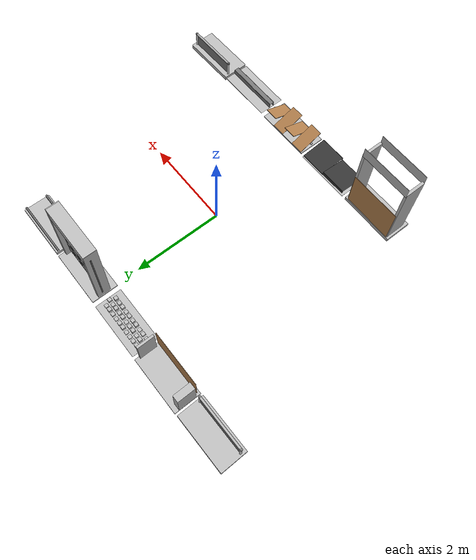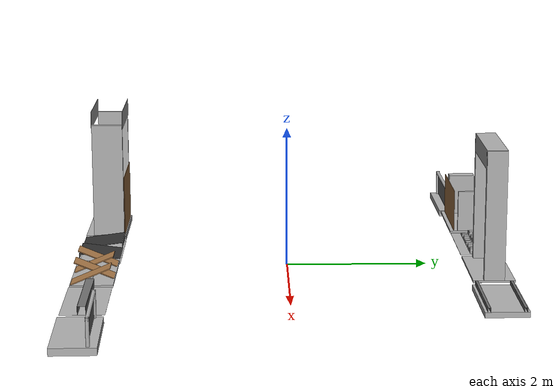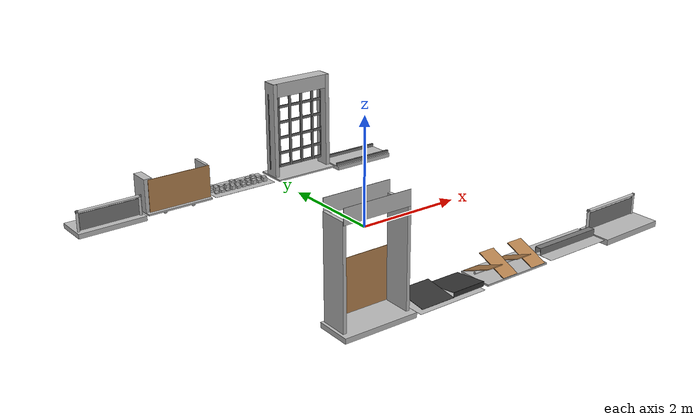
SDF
<?xml version="1.0" encoding="utf-8"?>
<sdf version='1.7'>
  <model name='field_elements'>
    <model name='frc2016_rockwall'>
      <pose frame=''>2.0377 -2.705 0.027 0 0 0</pose>
      <static>1</static>
      <link name='link'>
        <inertial>
          <mass>10</mass>
          <pose frame=''>0 0 0 0 -0 0</pose>
          <inertia>
            <ixx>0.327091</ixx>
            <ixy>0</ixy>
            <ixz>0</ixz>
            <iyy>1.37417</iyy>
            <iyz>0</iyz>
            <izz>1.64109</izz>
          </inertia>
        </inertial>
        <visual name='platform'>
          <pose frame=''>0 0 0.06432 0 -0 0</pose>
          <geometry>
            <box>
              <size>1.27 0.5969 0.003175</size>
            </box>
          </geometry>
        </visual>
        <collision name='platform'>
          <pose frame=''>0 0 0.06432 0 -0 0</pose>
          <geometry>
            <box>
              <size>1.27 0.5969 0.003175</size>
            </box>
          </geometry>
          <max_contacts>10</max_contacts>
          <surface>
            <contact>
              <ode/>
            </contact>
            <bounce/>
            <friction>
              <ode/>
            </friction>
          </surface>
        </collision>
        <visual name='up1'>
          <pose frame=''>0 0.05166 0.12537 0 -0 0</pose>
          <geometry>
            <box>
              <size>1.27 0.00462 0.11892</size>
            </box>
          </geometry>
          <material>
            <ambient>0.46 0.46 0.46 1</ambient>
            <diffuse>0.46 0.46 0.46 1</diffuse>
          </material>
        </visual>
        <collision name='up1'>
          <pose frame=''>0 0.05166 0.12537 0 -0 0</pose>
          <geometry>
            <box>
              <size>1.27 0.00462 0.11892</size>
            </box>
          </geometry>
          <max_contacts>10</max_contacts>
          <surface>
            <contact>
              <ode/>
            </contact>
            <bounce/>
            <friction>
              <ode/>
            </friction>
          </surface>
        </collision>
        <visual name='up2'>
          <pose frame=''>0 -0.05801 0.12537 0 -0 0</pose>
          <geometry>
            <box>
              <size>1.27 0.00462 0.11892</size>
            </box>
          </geometry>
          <material>
            <ambient>0.46 0.46 0.46 1</ambient>
            <diffuse>0.46 0.46 0.46 1</diffuse>
          </material>
        </visual>
        <collision name='up2'>
          <pose frame=''>0 -0.05801 0.12537 0 -0 0</pose>
          <geometry>
            <box>
              <size>1.27 0.00462 0.11892</size>
            </box>
          </geometry>
          <max_contacts>10</max_contacts>
          <surface>
            <contact>
              <ode/>
            </contact>
            <bounce/>
            <friction>
              <ode/>
            </friction>
          </surface>
        </collision>
        <visual name='top'>
          <pose frame=''>0 -0.00249 0.18252 0 -0 0</pose>
          <geometry>
            <box>
              <size>1.27 0.1143 0.00462</size>
            </box>
          </geometry>
          <material>
            <ambient>0.46 0.46 0.46 1</ambient>
            <diffuse>0.46 0.46 0.46 1</diffuse>
          </material>
        </visual>
        <collision name='top'>
          <pose frame=''>0 -0.00249 0.18252 0 -0 0</pose>
          <geometry>
            <box>
              <size>1.27 0.1143 0.00462</size>
            </box>
          </geometry>
          <max_contacts>10</max_contacts>
          <surface>
            <contact>
              <ode/>
            </contact>
            <bounce/>
            <friction>
              <ode/>
            </friction>
          </surface>
        </collision>
        <self_collide>0</self_collide>
        <kinematic>0</kinematic>
        <gravity>1</gravity>
      </link>
      <pose frame=''>-0.584117 1 0 0 -0 0</pose>
    </model>
    <model name='frc2016_moat'>
      <static>1</static>
      <pose frame=''>1.93647 2.80928 -0.019486 0 -0 0</pose>
      <link name='link'>
        <inertial>
          <mass>10</mass>
          <pose frame=''>0 0 0.06738 0 -0 0</pose>
          <inertia>
            <ixx>0.312195</ixx>
            <ixy>0</ixy>
            <ixz>0</ixz>
            <iyy>1.35927</iyy>
            <iyz>0</iyz>
            <izz>1.64109</izz>
          </inertia>
        </inertial>
        <visual name='platform'>
          <pose frame=''>0 0 0.0381 0 -0 0</pose>
          <geometry>
            <box>
              <size>1.27 0.5969 0.0762</size>
            </box>
          </geometry>
        </visual>
        <collision name='platform'>
          <pose frame=''>0 0 0.0381 0 -0 0</pose>
          <geometry>
            <box>
              <size>1.27 0.5969 0.0762</size>
            </box>
          </geometry>
          <max_contacts>10</max_contacts>
          <surface>
            <contact>
              <ode/>
            </contact>
            <bounce/>
            <friction>
              <ode/>
            </friction>
          </surface>
        </collision>
        <visual name='tube1_side1'>
          <pose frame=''>0 -0.25876 0.10301 0 -0 0</pose>
          <geometry>
            <box>
              <size>1.27 0.003175 0.0635</size>
            </box>
          </geometry>
          <material>
            <ambient>0.46 0.46 0.46 1</ambient>
            <diffuse>0.46 0.46 0.46 1</diffuse>
          </material>
        </visual>
        <collision name='tube1_side1'>
          <pose frame=''>0 -0.25876 0.10301 0 -0 0</pose>
          <geometry>
            <box>
              <size>1.27 0.003175 0.0635</size>
            </box>
          </geometry>
          <max_contacts>10</max_contacts>
          <surface>
            <contact>
              <ode/>
            </contact>
            <bounce/>
            <friction>
              <ode/>
            </friction>
          </surface>
        </collision>
        <visual name='tube1_side2'>
          <pose frame=''>0 -0.22384 0.10301 0 -0 0</pose>
          <geometry>
            <box>
              <size>1.27 0.003175 0.0635</size>
            </box>
          </geometry>
          <material>
            <ambient>0.46 0.46 0.46 1</ambient>
            <diffuse>0.46 0.46 0.46 1</diffuse>
          </material>
        </visual>
        <collision name='tube1_side2'>
          <pose frame=''>0 -0.22384 0.10301 0 -0 0</pose>
          <geometry>
            <box>
              <size>1.27 0.003175 0.0635</size>
            </box>
          </geometry>
          <max_contacts>10</max_contacts>
          <surface>
            <contact>
              <ode/>
            </contact>
            <bounce/>
            <friction>
              <ode/>
            </friction>
          </surface>
        </collision>
        <visual name='tube1_top'>
          <pose frame=''>0 -0.2413 0.13317 0 -0 0</pose>
          <geometry>
            <box>
              <size>1.27 0.0381 0.003175</size>
            </box>
          </geometry>
          <material>
            <ambient>0.46 0.46 0.46 1</ambient>
            <diffuse>0.46 0.46 0.46 1</diffuse>
          </material>
        </visual>
        <collision name='tube1_top'>
          <pose frame=''>0 -0.2413 0.13317 0 -0 0</pose>
          <geometry>
            <box>
              <size>1.27 0.0381 0.003175</size>
            </box>
          </geometry>
          <max_contacts>10</max_contacts>
          <surface>
            <contact>
              <ode/>
            </contact>
            <bounce/>
            <friction>
              <ode/>
            </friction>
          </surface>
        </collision>
        <visual name='tube2_side1'>
          <pose frame=''>0 0.22384 0.10301 0 -0 0</pose>
          <geometry>
            <box>
              <size>1.27 0.003175 0.0635</size>
            </box>
          </geometry>
          <material>
            <ambient>0.46 0.46 0.46 1</ambient>
            <diffuse>0.46 0.46 0.46 1</diffuse>
          </material>
        </visual>
        <collision name='tube2_side1'>
          <pose frame=''>0 0.22384 0.10301 0 -0 0</pose>
          <geometry>
            <box>
              <size>1.27 0.003175 0.0635</size>
            </box>
          </geometry>
          <max_contacts>10</max_contacts>
          <surface>
            <contact>
              <ode/>
            </contact>
            <bounce/>
            <friction>
              <ode/>
            </friction>
          </surface>
        </collision>
        <visual name='tube2_side2'>
          <pose frame=''>0 0.25876 0.10301 0 -0 0</pose>
          <geometry>
            <box>
              <size>1.27 0.003175 0.0635</size>
            </box>
          </geometry>
          <material>
            <ambient>0.46 0.46 0.46 1</ambient>
            <diffuse>0.46 0.46 0.46 1</diffuse>
          </material>
        </visual>
        <collision name='tube2_side2'>
          <pose frame=''>0 0.25876 0.10301 0 -0 0</pose>
          <geometry>
            <box>
              <size>1.27 0.003175 0.0635</size>
            </box>
          </geometry>
          <max_contacts>10</max_contacts>
          <surface>
            <contact>
              <ode/>
            </contact>
            <bounce/>
            <friction>
              <ode/>
            </friction>
          </surface>
        </collision>
        <visual name='tube2_top'>
          <pose frame=''>0 0.2413 0.13317 0 -0 0</pose>
          <geometry>
            <box>
              <size>1.27 0.0381 0.003175</size>
            </box>
          </geometry>
          <material>
            <ambient>0.46 0.46 0.46 1</ambient>
            <diffuse>0.46 0.46 0.46 1</diffuse>
          </material>
        </visual>
        <collision name='tube2_top'>
          <pose frame=''>0 0.2413 0.13317 0 -0 0</pose>
          <geometry>
            <box>
              <size>1.27 0.0381 0.003175</size>
            </box>
          </geometry>
          <max_contacts>10</max_contacts>
          <surface>
            <contact>
              <ode/>
            </contact>
            <bounce/>
            <friction>
              <ode/>
            </friction>
          </surface>
        </collision>
        <self_collide>0</self_collide>
        <kinematic>0</kinematic>
        <gravity>1</gravity>
      </link>
      <pose frame=''>1.49502 1 0 0 -0 0</pose>
    </model>
    <model name='frc2016_roughterrain'>
      <static>1</static>
      <pose frame=''>-0.796271 2.83126 -0.008615 0 -0 0</pose>
      <link name='link'>
        <visual name='platform'>
          <pose frame=''>0 0 0.08269 0 -0 0</pose>
          <geometry>
            <box>
              <size>1.27 0.5969 0.003175</size>
            </box>
          </geometry>
        </visual>
        <collision name='platform'>
          <pose frame=''>0 0 0.08269 0 -0 0</pose>
          <geometry>
            <box>
              <size>1.27 0.5969 0.003175</size>
            </box>
          </geometry>
          <max_contacts>10</max_contacts>
          <surface>
            <contact>
              <ode/>
            </contact>
            <bounce/>
            <friction>
              <ode/>
            </friction>
          </surface>
        </collision>
        <visual name='row1_block1_sm'>
          <pose frame=''>0.51435 0.1143 0.09698 0 -0 0</pose>
          <geometry>
            <box>
              <size>0.0762 0.0762 0.0254</size>
            </box>
          </geometry>
        </visual>
        <collision name='row1_block1_sm'>
          <pose frame=''>0.51435 0.1143 0.09698 0 -0 0</pose>
          <geometry>
            <box>
              <size>0.0762 0.0762 0.0254</size>
            </box>
          </geometry>
          <max_contacts>10</max_contacts>
          <surface>
            <contact>
              <ode/>
            </contact>
            <bounce/>
            <friction>
              <ode/>
            </friction>
          </surface>
        </collision>
        <visual name='row1_block2_lg'>
          <pose frame=''>0.40005 0.1143 0.12238 0 -0 0</pose>
          <geometry>
            <box>
              <size>0.0762 0.0762 0.0762</size>
            </box>
          </geometry>
        </visual>
        <collision name='row1_block2_lg'>
          <pose frame=''>0.40005 0.1143 0.12238 0 -0 0</pose>
          <geometry>
            <box>
              <size>0.0762 0.0762 0.0762</size>
            </box>
          </geometry>
          <max_contacts>10</max_contacts>
          <surface>
            <contact>
              <ode/>
            </contact>
            <bounce/>
            <friction>
              <ode/>
            </friction>
          </surface>
        </collision>
        <visual name='row1_block3_md'>
          <pose frame=''>0.28575 0.1143 0.10968 0 -0 0</pose>
          <geometry>
            <box>
              <size>0.0762 0.0762 0.0508</size>
            </box>
          </geometry>
        </visual>
        <collision name='row1_block3_md'>
          <pose frame=''>0.28575 0.1143 0.10968 0 -0 0</pose>
          <geometry>
            <box>
              <size>0.0762 0.0762 0.0508</size>
            </box>
          </geometry>
          <max_contacts>10</max_contacts>
          <surface>
            <contact>
              <ode/>
            </contact>
            <bounce/>
            <friction>
              <ode/>
            </friction>
          </surface>
        </collision>
        <visual name='row1_block4_sm'>
          <pose frame=''>0.17145 0.1143 0.09698 0 -0 0</pose>
          <geometry>
            <box>
              <size>0.0762 0.0762 0.0254</size>
            </box>
          </geometry>
        </visual>
        <collision name='row1_block4_sm'>
          <pose frame=''>0.17145 0.1143 0.09698 0 -0 0</pose>
          <geometry>
            <box>
              <size>0.0762 0.0762 0.0254</size>
            </box>
          </geometry>
          <max_contacts>10</max_contacts>
          <surface>
            <contact>
              <ode/>
            </contact>
            <bounce/>
            <friction>
              <ode/>
            </friction>
          </surface>
        </collision>
        <visual name='row1_block5_md'>
          <pose frame=''>0.05715 0.1143 0.10968 0 -0 0</pose>
          <geometry>
            <box>
              <size>0.0762 0.0762 0.0508</size>
            </box>
          </geometry>
        </visual>
        <collision name='row1_block5_md'>
          <pose frame=''>0.05715 0.1143 0.10968 0 -0 0</pose>
          <geometry>
            <box>
              <size>0.0762 0.0762 0.0508</size>
            </box>
          </geometry>
          <max_contacts>10</max_contacts>
          <surface>
            <contact>
              <ode/>
            </contact>
            <bounce/>
            <friction>
              <ode/>
            </friction>
          </surface>
        </collision>
        <visual name='row1_block6_lg'>
          <pose frame=''>-0.05715 0.1143 0.12238 0 -0 0</pose>
          <geometry>
            <box>
              <size>0.0762 0.0762 0.0762</size>
            </box>
          </geometry>
        </visual>
        <collision name='row1_block6_lg'>
          <pose frame=''>-0.05715 0.1143 0.12238 0 -0 0</pose>
          <geometry>
            <box>
              <size>0.0762 0.0762 0.0762</size>
            </box>
          </geometry>
          <max_contacts>10</max_contacts>
          <surface>
            <contact>
              <ode/>
            </contact>
            <bounce/>
            <friction>
              <ode/>
            </friction>
          </surface>
        </collision>
        <visual name='row1_block7_sm'>
          <pose frame=''>-0.17145 0.1143 0.09698 0 -0 0</pose>
          <geometry>
            <box>
              <size>0.0762 0.0762 0.0254</size>
            </box>
          </geometry>
        </visual>
        <collision name='row1_block7_sm'>
          <pose frame=''>-0.17145 0.1143 0.09698 0 -0 0</pose>
          <geometry>
            <box>
              <size>0.0762 0.0762 0.0254</size>
            </box>
          </geometry>
          <max_contacts>10</max_contacts>
          <surface>
            <contact>
              <ode/>
            </contact>
            <bounce/>
            <friction>
              <ode/>
            </friction>
          </surface>
        </collision>
        <visual name='row1_block8_sm'>
          <pose frame=''>-0.28575 0.1143 0.09698 0 -0 0</pose>
          <geometry>
            <box>
              <size>0.0762 0.0762 0.0254</size>
            </box>
          </geometry>
        </visual>
        <collision name='row1_block8_sm'>
          <pose frame=''>-0.28575 0.1143 0.09698 0 -0 0</pose>
          <geometry>
            <box>
              <size>0.0762 0.0762 0.0254</size>
            </box>
          </geometry>
          <max_contacts>10</max_contacts>
          <surface>
            <contact>
              <ode/>
            </contact>
            <bounce/>
            <friction>
              <ode/>
            </friction>
          </surface>
        </collision>
        <visual name='row1_block9_md'>
          <pose frame=''>-0.40005 0.1143 0.10968 0 -0 0</pose>
          <geometry>
            <box>
              <size>0.0762 0.0762 0.0508</size>
            </box>
          </geometry>
        </visual>
        <collision name='row1_block9_md'>
          <pose frame=''>-0.40005 0.1143 0.10968 0 -0 0</pose>
          <geometry>
            <box>
              <size>0.0762 0.0762 0.0508</size>
            </box>
          </geometry>
          <max_contacts>10</max_contacts>
          <surface>
            <contact>
              <ode/>
            </contact>
            <bounce/>
            <friction>
              <ode/>
            </friction>
          </surface>
        </collision>
        <visual name='row1_block10_lg'>
          <pose frame=''>-0.51435 0.1143 0.12238 0 -0 0</pose>
          <geometry>
            <box>
              <size>0.0762 0.0762 0.0762</size>
            </box>
          </geometry>
        </visual>
        <collision name='row1_block10_lg'>
          <pose frame=''>-0.51435 0.1143 0.12238 0 -0 0</pose>
          <geometry>
            <box>
              <size>0.0762 0.0762 0.0762</size>
            </box>
          </geometry>
          <max_contacts>10</max_contacts>
          <surface>
            <contact>
              <ode/>
            </contact>
            <bounce/>
            <friction>
              <ode/>
            </friction>
          </surface>
        </collision>
        <visual name='row2_block1_md'>
          <pose frame=''>0.5715 0 0.10968 0 -0 0</pose>
          <geometry>
            <box>
              <size>0.0762 0.0762 0.0508</size>
            </box>
          </geometry>
        </visual>
        <collision name='row2_block1_md'>
          <pose frame=''>0.5715 0 0.10968 0 -0 0</pose>
          <geometry>
            <box>
              <size>0.0762 0.0762 0.0508</size>
            </box>
          </geometry>
          <max_contacts>10</max_contacts>
          <surface>
            <contact>
              <ode/>
            </contact>
            <bounce/>
            <friction>
              <ode/>
            </friction>
          </surface>
        </collision>
        <visual name='row2_block2_sm'>
          <pose frame=''>0.4572 0 0.09698 0 -0 0</pose>
          <geometry>
            <box>
              <size>0.0762 0.0762 0.0254</size>
            </box>
          </geometry>
        </visual>
        <collision name='row2_block2_sm'>
          <pose frame=''>0.4572 0 0.09698 0 -0 0</pose>
          <geometry>
            <box>
              <size>0.0762 0.0762 0.0254</size>
            </box>
          </geometry>
          <max_contacts>10</max_contacts>
          <surface>
            <contact>
              <ode/>
            </contact>
            <bounce/>
            <friction>
              <ode/>
            </friction>
          </surface>
        </collision>
        <visual name='row2_block3_lg'>
          <pose frame=''>0.3429 0 0.12238 0 -0 0</pose>
          <geometry>
            <box>
              <size>0.0762 0.0762 0.0762</size>
            </box>
          </geometry>
        </visual>
        <collision name='row2_block3_lg'>
          <pose frame=''>0.3429 0 0.12238 0 -0 0</pose>
          <geometry>
            <box>
              <size>0.0762 0.0762 0.0762</size>
            </box>
          </geometry>
          <max_contacts>10</max_contacts>
          <surface>
            <contact>
              <ode/>
            </contact>
            <bounce/>
            <friction>
              <ode/>
            </friction>
          </surface>
        </collision>
        <visual name='row2_block4_md'>
          <pose frame=''>0.2286 0 0.10968 0 -0 0</pose>
          <geometry>
            <box>
              <size>0.0762 0.0762 0.0508</size>
            </box>
          </geometry>
        </visual>
        <collision name='row2_block4_md'>
          <pose frame=''>0.2286 0 0.10968 0 -0 0</pose>
          <geometry>
            <box>
              <size>0.0762 0.0762 0.0508</size>
            </box>
          </geometry>
          <max_contacts>10</max_contacts>
          <surface>
            <contact>
              <ode/>
            </contact>
            <bounce/>
            <friction>
              <ode/>
            </friction>
          </surface>
        </collision>
        <visual name='row2_block5_lg'>
          <pose frame=''>0.1143 0 0.12238 0 -0 0</pose>
          <geometry>
            <box>
              <size>0.0762 0.0762 0.0762</size>
            </box>
          </geometry>
        </visual>
        <collision name='row2_block5_lg'>
          <pose frame=''>0.1143 0 0.12238 0 -0 0</pose>
          <geometry>
            <box>
              <size>0.0762 0.0762 0.0762</size>
            </box>
          </geometry>
          <max_contacts>10</max_contacts>
          <surface>
            <contact>
              <ode/>
            </contact>
            <bounce/>
            <friction>
              <ode/>
            </friction>
          </surface>
        </collision>
        <visual name='row2_block6_sm'>
          <pose frame=''>0 0 0.09698 0 -0 0</pose>
          <geometry>
            <box>
              <size>0.0762 0.0762 0.0254</size>
            </box>
          </geometry>
        </visual>
        <collision name='row2_block6_sm'>
          <pose frame=''>0 0 0.09698 0 -0 0</pose>
          <geometry>
            <box>
              <size>0.0762 0.0762 0.0254</size>
            </box>
          </geometry>
          <max_contacts>10</max_contacts>
          <surface>
            <contact>
              <ode/>
            </contact>
            <bounce/>
            <friction>
              <ode/>
            </friction>
          </surface>
        </collision>
        <visual name='row2_block7_md'>
          <pose frame=''>-0.1143 0 0.10968 0 -0 0</pose>
          <geometry>
            <box>
              <size>0.0762 0.0762 0.0508</size>
            </box>
          </geometry>
        </visual>
        <collision name='row2_block7_md'>
          <pose frame=''>-0.1143 0 0.10968 0 -0 0</pose>
          <geometry>
            <box>
              <size>0.0762 0.0762 0.0508</size>
            </box>
          </geometry>
          <max_contacts>10</max_contacts>
          <surface>
            <contact>
              <ode/>
            </contact>
            <bounce/>
            <friction>
              <ode/>
            </friction>
          </surface>
        </collision>
        <visual name='row2_block8_lg'>
          <pose frame=''>-0.2286 0 0.12238 0 -0 0</pose>
          <geometry>
            <box>
              <size>0.0762 0.0762 0.0762</size>
            </box>
          </geometry>
        </visual>
        <collision name='row2_block8_lg'>
          <pose frame=''>-0.2286 0 0.12238 0 -0 0</pose>
          <geometry>
            <box>
              <size>0.0762 0.0762 0.0762</size>
            </box>
          </geometry>
          <max_contacts>10</max_contacts>
          <surface>
            <contact>
              <ode/>
            </contact>
            <bounce/>
            <friction>
              <ode/>
            </friction>
          </surface>
        </collision>
        <visual name='row2_block9_sm'>
          <pose frame=''>-0.3429 0 0.09698 0 -0 0</pose>
          <geometry>
            <box>
              <size>0.0762 0.0762 0.0254</size>
            </box>
          </geometry>
        </visual>
        <collision name='row2_block9_sm'>
          <pose frame=''>-0.3429 0 0.09698 0 -0 0</pose>
          <geometry>
            <box>
              <size>0.0762 0.0762 0.0254</size>
            </box>
          </geometry>
          <max_contacts>10</max_contacts>
          <surface>
            <contact>
              <ode/>
            </contact>
            <bounce/>
            <friction>
              <ode/>
            </friction>
          </surface>
        </collision>
        <visual name='row2_block10_lg'>
          <pose frame=''>-0.4572 0 0.12238 0 -0 0</pose>
          <geometry>
            <box>
              <size>0.0762 0.0762 0.0762</size>
            </box>
          </geometry>
        </visual>
        <collision name='row2_block10_lg'>
          <pose frame=''>-0.4572 0 0.12238 0 -0 0</pose>
          <geometry>
            <box>
              <size>0.0762 0.0762 0.0762</size>
            </box>
          </geometry>
          <max_contacts>10</max_contacts>
          <surface>
            <contact>
              <ode/>
            </contact>
            <bounce/>
            <friction>
              <ode/>
            </friction>
          </surface>
        </collision>
        <visual name='row2_block11_md'>
          <pose frame=''>-0.5715 0 0.10968 0 -0 0</pose>
          <geometry>
            <box>
              <size>0.0762 0.0762 0.0508</size>
            </box>
          </geometry>
        </visual>
        <collision name='row2_block11_md'>
          <pose frame=''>-0.5715 0 0.10968 0 -0 0</pose>
          <geometry>
            <box>
              <size>0.0762 0.0762 0.0508</size>
            </box>
          </geometry>
          <max_contacts>10</max_contacts>
          <surface>
            <contact>
              <ode/>
            </contact>
            <bounce/>
            <friction>
              <ode/>
            </friction>
          </surface>
        </collision>
        <visual name='row3_block1_lg'>
          <pose frame=''>0.51435 -0.1143 0.12238 0 -0 0</pose>
          <geometry>
            <box>
              <size>0.0762 0.0762 0.0762</size>
            </box>
          </geometry>
        </visual>
        <collision name='row3_block1_lg'>
          <pose frame=''>0.51435 -0.1143 0.12238 0 -0 0</pose>
          <geometry>
            <box>
              <size>0.0762 0.0762 0.0762</size>
            </box>
          </geometry>
          <max_contacts>10</max_contacts>
          <surface>
            <contact>
              <ode/>
            </contact>
            <bounce/>
            <friction>
              <ode/>
            </friction>
          </surface>
        </collision>
        <visual name='row3_block2_md'>
          <pose frame=''>0.40005 -0.1143 0.10968 0 -0 0</pose>
          <geometry>
            <box>
              <size>0.0762 0.0762 0.0508</size>
            </box>
          </geometry>
        </visual>
        <collision name='row3_block2_md'>
          <pose frame=''>0.40005 -0.1143 0.10968 0 -0 0</pose>
          <geometry>
            <box>
              <size>0.0762 0.0762 0.0508</size>
            </box>
          </geometry>
          <max_contacts>10</max_contacts>
          <surface>
            <contact>
              <ode/>
            </contact>
            <bounce/>
            <friction>
              <ode/>
            </friction>
          </surface>
        </collision>
        <visual name='row3_block3_lg'>
          <pose frame=''>0.28575 -0.1143 0.12238 0 -0 0</pose>
          <geometry>
            <box>
              <size>0.0762 0.0762 0.0762</size>
            </box>
          </geometry>
        </visual>
        <collision name='row3_block3_lg'>
          <pose frame=''>0.28575 -0.1143 0.12238 0 -0 0</pose>
          <geometry>
            <box>
              <size>0.0762 0.0762 0.0762</size>
            </box>
          </geometry>
          <max_contacts>10</max_contacts>
          <surface>
            <contact>
              <ode/>
            </contact>
            <bounce/>
            <friction>
              <ode/>
            </friction>
          </surface>
        </collision>
        <visual name='row3_block4_sm'>
          <pose frame=''>0.17145 -0.1143 0.09698 0 -0 0</pose>
          <geometry>
            <box>
              <size>0.0762 0.0762 0.0254</size>
            </box>
          </geometry>
        </visual>
        <collision name='row3_block4_sm'>
          <pose frame=''>0.17145 -0.1143 0.09698 0 -0 0</pose>
          <geometry>
            <box>
              <size>0.0762 0.0762 0.0254</size>
            </box>
          </geometry>
          <max_contacts>10</max_contacts>
          <surface>
            <contact>
              <ode/>
            </contact>
            <bounce/>
            <friction>
              <ode/>
            </friction>
          </surface>
        </collision>
        <visual name='row3_block5_md'>
          <pose frame=''>0.05715 -0.1143 0.10968 0 -0 0</pose>
          <geometry>
            <box>
              <size>0.0762 0.0762 0.0508</size>
            </box>
          </geometry>
        </visual>
        <collision name='row3_block5_md'>
          <pose frame=''>0.05715 -0.1143 0.10968 0 -0 0</pose>
          <geometry>
            <box>
              <size>0.0762 0.0762 0.0508</size>
            </box>
          </geometry>
          <max_contacts>10</max_contacts>
          <surface>
            <contact>
              <ode/>
            </contact>
            <bounce/>
            <friction>
              <ode/>
            </friction>
          </surface>
        </collision>
        <visual name='row3_block6_md'>
          <pose frame=''>-0.05715 -0.1143 0.10968 0 -0 0</pose>
          <geometry>
            <box>
              <size>0.0762 0.0762 0.0508</size>
            </box>
          </geometry>
        </visual>
        <collision name='row3_block6_md'>
          <pose frame=''>-0.05715 -0.1143 0.10968 0 -0 0</pose>
          <geometry>
            <box>
              <size>0.0762 0.0762 0.0508</size>
            </box>
          </geometry>
          <max_contacts>10</max_contacts>
          <surface>
            <contact>
              <ode/>
            </contact>
            <bounce/>
            <friction>
              <ode/>
            </friction>
          </surface>
        </collision>
        <visual name='row3_block7_lg'>
          <pose frame=''>-0.17145 -0.1143 0.12238 0 -0 0</pose>
          <geometry>
            <box>
              <size>0.0762 0.0762 0.0762</size>
            </box>
          </geometry>
        </visual>
        <collision name='row3_block7_lg'>
          <pose frame=''>-0.17145 -0.1143 0.12238 0 -0 0</pose>
          <geometry>
            <box>
              <size>0.0762 0.0762 0.0762</size>
            </box>
          </geometry>
          <max_contacts>10</max_contacts>
          <surface>
            <contact>
              <ode/>
            </contact>
            <bounce/>
            <friction>
              <ode/>
            </friction>
          </surface>
        </collision>
        <visual name='row3_block8_sm'>
          <pose frame=''>-0.28575 -0.1143 0.09698 0 -0 0</pose>
          <geometry>
            <box>
              <size>0.0762 0.0762 0.0254</size>
            </box>
          </geometry>
        </visual>
        <collision name='row3_block8_sm'>
          <pose frame=''>-0.28575 -0.1143 0.09698 0 -0 0</pose>
          <geometry>
            <box>
              <size>0.0762 0.0762 0.0254</size>
            </box>
          </geometry>
          <max_contacts>10</max_contacts>
          <surface>
            <contact>
              <ode/>
            </contact>
            <bounce/>
            <friction>
              <ode/>
            </friction>
          </surface>
        </collision>
        <visual name='row3_block9_md'>
          <pose frame=''>-0.40005 -0.1143 0.10968 0 -0 0</pose>
          <geometry>
            <box>
              <size>0.0762 0.0762 0.0508</size>
            </box>
          </geometry>
        </visual>
        <collision name='row3_block9_md'>
          <pose frame=''>-0.40005 -0.1143 0.10968 0 -0 0</pose>
          <geometry>
            <box>
              <size>0.0762 0.0762 0.0508</size>
            </box>
          </geometry>
          <max_contacts>10</max_contacts>
          <surface>
            <contact>
              <ode/>
            </contact>
            <bounce/>
            <friction>
              <ode/>
            </friction>
          </surface>
        </collision>
        <visual name='row3_block10_sm'>
          <pose frame=''>-0.51435 -0.1143 0.09698 0 -0 0</pose>
          <geometry>
            <box>
              <size>0.0762 0.0762 0.0254</size>
            </box>
          </geometry>
        </visual>
        <collision name='row3_block10_sm'>
          <pose frame=''>-0.51435 -0.1143 0.09698 0 -0 0</pose>
          <geometry>
            <box>
              <size>0.0762 0.0762 0.0254</size>
            </box>
          </geometry>
          <max_contacts>10</max_contacts>
          <surface>
            <contact>
              <ode/>
            </contact>
            <bounce/>
            <friction>
              <ode/>
            </friction>
          </surface>
        </collision>
        <self_collide>0</self_collide>
        <kinematic>0</kinematic>
        <gravity>1</gravity>
      </link>
      <pose frame=''>3 1 0 0 -0 0</pose>
    </model>
    <model name='frc2016_ramparts'>
      <pose frame=''>-0.65617 -2.70099 0.015 0 -0 0</pose>
      <static>1</static>
      <link name='link'>
        <visual name='platform'>
          <pose frame=''>0 0 0 0 -0 0</pose>
          <geometry>
            <box>
              <size>1.27 0.5969 0.003175</size>
            </box>
          </geometry>
        </visual>
        <collision name='platform'>
          <pose frame=''>0 0 0.06967 0 -0 0</pose>
          <geometry>
            <box>
              <size>1.27 0.5969 0.003175</size>
            </box>
          </geometry>
          <max_contacts>10</max_contacts>
          <surface>
            <contact>
              <ode/>
            </contact>
            <bounce/>
            <friction>
              <ode/>
            </friction>
          </surface>
        </collision>
        <visual name='ramp1'>
          <pose frame=''>0.30472 0.00588 0.1109 -0.13 0 0</pose>
          <geometry>
            <box>
              <size>0.60957 0.588891 0.00462</size>
            </box>
          </geometry>
          <material>
            <ambient>0.2 0.2 0.2 1</ambient>
            <diffuse>0.2 0.2 0.2 1</diffuse>
          </material>
        </visual>
        <collision name='ramp1'>
          <pose frame=''>0.30472 0.00588 0.1109 -0.13 0 0</pose>
          <geometry>
            <box>
              <size>0.60957 0.588891 0.00462</size>
            </box>
          </geometry>
          <max_contacts>10</max_contacts>
          <surface>
            <contact>
              <ode/>
            </contact>
            <bounce/>
            <friction>
              <ode/>
            </friction>
          </surface>
        </collision>
        <visual name='up1'>
          <pose frame=''>0.30472 -0.28806 0.11072 0 -0 0</pose>
          <geometry>
            <box>
              <size>0.60957 0.00462 0.07872</size>
            </box>
          </geometry>
          <material>
            <ambient>0.2 0.2 0.2 1</ambient>
            <diffuse>0.2 0.2 0.2 1</diffuse>
          </material>
        </visual>
        <collision name='up1'>
          <pose frame=''>0.30472 -0.28806 0.11072 0 -0 0</pose>
          <geometry>
            <box>
              <size>0.60957 0.00462 0.07872</size>
            </box>
          </geometry>
          <max_contacts>10</max_contacts>
          <surface>
            <contact>
              <ode/>
            </contact>
            <bounce/>
            <friction>
              <ode/>
            </friction>
          </surface>
        </collision>
        <visual name='ramp2'>
          <pose frame=''>-0.30472 -0.00619 0.1109 0.13 -0 0</pose>
          <geometry>
            <box>
              <size>0.60957 0.588891 0.00462</size>
            </box>
          </geometry>
          <material>
            <ambient>0.2 0.2 0.2 1</ambient>
            <diffuse>0.2 0.2 0.2 1</diffuse>
          </material>
        </visual>
        <collision name='ramp2'>
          <pose frame=''>-0.30472 -0.00619 0.1109 0.13 -0 0</pose>
          <geometry>
            <box>
              <size>0.60957 0.588891 0.00462</size>
            </box>
          </geometry>
          <max_contacts>10</max_contacts>
          <surface>
            <contact>
              <ode/>
            </contact>
            <bounce/>
            <friction>
              <ode/>
            </friction>
          </surface>
        </collision>
        <visual name='up2'>
          <pose frame=''>-0.30472 0.28806 0.11072 0 -0 0</pose>
          <geometry>
            <box>
              <size>0.60957 0.00462 0.07872</size>
            </box>
          </geometry>
          <material>
            <ambient>0.2 0.2 0.2 1</ambient>
            <diffuse>0.2 0.2 0.2 1</diffuse>
          </material>
        </visual>
        <collision name='up2'>
          <pose frame=''>-0.30472 0.28806 0.11072 0 -0 0</pose>
          <geometry>
            <box>
              <size>0.60957 0.00462 0.07872</size>
            </box>
          </geometry>
          <max_contacts>10</max_contacts>
          <surface>
            <contact>
              <ode/>
            </contact>
            <bounce/>
            <friction>
              <ode/>
            </friction>
          </surface>
        </collision>
        <self_collide>0</self_collide>
        <kinematic>0</kinematic>
        <gravity>1</gravity>
      </link>
      <pose frame=''>-2.431 3 0 0 -0 0</pose>
    </model>
    <model name='frc2016_lowbar_0_0'>
      <pose frame=''>-3.45668 2.8117 -5e-06 2.5e-05 -4e-06 0.009735</pose>
      <link name='base'>
        <inertial>
          <mass>50</mass>
          <inertia>
            <ixx>0.035543</ixx>
            <ixy>0</ixy>
            <ixz>0</ixz>
            <iyy>0.134412</iyy>
            <iyz>0</iyz>
            <izz>0.165376</izz>
          </inertia>
        </inertial>
        <visual name='platform'>
          <pose frame=''>0 0 0.039065 0 -0 0</pose>
          <geometry>
            <box>
             <size>1.27 0.60 0.089</size>
            </box>
          </geometry>
        </visual>
        <collision name='platform'>
          <pose frame=''>0 0 0.039065 0 -0 0</pose>
          <geometry>
            <box>
              <size>1.27 0.60 0.089</size>
            </box>
          </geometry>
          <max_contacts>10</max_contacts>
          <surface>
            <contact>
              <ode/>
            </contact>
            <bounce/>
            <friction>
              <ode/>
            </friction>
          </surface>
        </collision>
        <visual name='right_column'>
          <pose frame=''>-0.57845 -0.18464 0.26863 0 -0 0</pose>
          <geometry>
            <cylinder>
              <radius>0.0254</radius>
              <length>0.381</length>
            </cylinder>
          </geometry>
        </visual>
        <collision name='right_column'>
          <pose frame=''>-0.57845 -0.18464 0.26863 0 -0 0</pose>
          <geometry>
            <cylinder>
              <radius>0.0254</radius>
              <length>0.381</length>
            </cylinder>
          </geometry>
          <max_contacts>10</max_contacts>
          <surface>
            <contact>
              <ode/>
            </contact>
            <bounce/>
            <friction>
              <ode/>
            </friction>
          </surface>
        </collision>
        <visual name='left_column'>
          <pose frame=''>0.57845 -0.18464 0.26863 0 -0 0</pose>
          <geometry>
            <cylinder>
              <radius>0.0254</radius>
              <length>0.381</length>
            </cylinder>
          </geometry>
        </visual>
        <collision name='left_column'>
          <pose frame=''>0.57845 -0.18464 0.26863 0 -0 0</pose>
          <geometry>
            <cylinder>
              <radius>0.0254</radius>
              <length>0.381</length>
            </cylinder>
          </geometry>
          <max_contacts>10</max_contacts>
          <surface>
            <contact>
              <ode/>
            </contact>
            <bounce/>
            <friction>
              <ode/>
            </friction>
          </surface>
        </collision>
        <visual name='horizontal'>
          <pose frame=''>0 -0.18464 0.43556 0 1.5707 0</pose>
          <geometry>
            <cylinder>
              <radius>0.0254</radius>
              <length>1.2018</length>
            </cylinder>
          </geometry>
        </visual>
        <collision name='horizontal'>
          <pose frame=''>0 -0.18464 0.43556 0 1.5707 0</pose>
          <geometry>
            <cylinder>
              <radius>0.0254</radius>
              <length>1.2018</length>
            </cylinder>
          </geometry>
          <max_contacts>10</max_contacts>
          <surface>
            <contact>
              <ode/>
            </contact>
            <bounce/>
            <friction>
              <ode/>
            </friction>
          </surface>
        </collision>
        <self_collide>0</self_collide>
        <kinematic>0</kinematic>
        <gravity>1</gravity>
      </link>
      <link name='wall'>
        <pose frame=''>0 -0.1778 0.24323 0 -0 0</pose>
        <inertial>
          <mass>1</mass>
          <inertia>
            <ixx>0.00774528</ixx>
            <ixy>0</ixy>
            <ixz>0</ixz>
            <iyy>0.116613</iyy>
            <iyz>0</iyz>
            <izz>0.108874</izz>
          </inertia>
        </inertial>
        <visual name='visual'>
          <geometry>
            <box>
              <size>1.1176 0.00635 0.3</size>
            </box>
          </geometry>
          <material>
            <ambient>0.46 0.46 0.46 1</ambient>
            <diffuse>0.46 0.46 0.46 1</diffuse>
          </material>
        </visual>
        <collision name='collision'>
          <geometry>
            <box>
              <size>1.143 0.00635 0.3</size>
            </box>
          </geometry>
          <max_contacts>10</max_contacts>
          <surface>
            <contact>
              <ode/>
            </contact>
            <bounce/>
            <friction>
              <ode/>
            </friction>
          </surface>
        </collision>
        <self_collide>0</self_collide>
        <kinematic>0</kinematic>
        <gravity>1</gravity>
      </link>
      <joint name='bar_joint' type='revolute'>
        <pose frame=''>0 0 0.36378 0 -0 0</pose>
        <parent>base</parent>
        <child>wall</child>
        <axis>
          <xyz>1 0 0</xyz>
          <limit>
            <lower>-1.5707</lower>
            <upper>1.5707</upper>
          </limit>
          <use_parent_model_frame>0</use_parent_model_frame>
          <dynamics>
            <damping>1</damping>
            <friction>1</friction>
            <spring_reference>0</spring_reference>
            <spring_stiffness>0</spring_stiffness>
          </dynamics>
        </axis>
      </joint>
      <pose frame=''>-3.451 3 0 0 -0 0</pose>
    </model>
    <model name='frc2016_sallyport'>
      <pose frame=''>-2.13787 2.83352 0 0 0 0</pose>
      <link name='base'>
        <inertial>
          <mass>50</mass>
          <pose frame=''>0 0 0.35406 0 -0 0</pose>
          <inertia>
            <ixx>0.727808</ixx>
            <ixy>0</ixy>
            <ixz>0</ixz>
            <iyy>1.77488</iyy>
            <iyz>0</iyz>
            <izz>1.64109</izz>
          </inertia>
        </inertial>
        <visual name='platform'>
          <pose frame=''>0 0 0.075 0 -0 0</pose>
          <geometry>
            <box>
              <size>1.27 0.5969 0.03</size>
            </box>
          </geometry>
        </visual>
        <collision name='platform'>
          <pose frame=''>0 0 0.075 0 -0 0</pose>
          <geometry>
            <box>
              <size>1.27 0.5969 0.03</size>
            </box>
          </geometry>
          <max_contacts>10</max_contacts>
          <surface>
            <contact>
              <ode/>
            </contact>
            <bounce/>
            <friction>
              <ode/>
            </friction>
          </surface>
        </collision>
        <visual name='left_column'>
          <pose frame=''>-0.5588 0.00318 0.38876 0 -0 0</pose>
          <geometry>
            <box>
              <size>0.1524 0.38735 0.635</size>
            </box>
          </geometry>
        </visual>
        <collision name='left_column'>
          <pose frame=''>-0.5588 0.00318 0.38876 0 -0 0</pose>
          <geometry>
            <box>
              <size>0.1524 0.38735 0.635</size>
            </box>
          </geometry>
          <max_contacts>10</max_contacts>
          <surface>
            <contact>
              <ode/>
            </contact>
            <bounce/>
            <friction>
              <ode/>
            </friction>
          </surface>
        </collision>
        <visual name='right_column'>
          <pose frame=''>0.6096 0.00635 0.38876 0 -0 0</pose>
          <geometry>
            <box>
              <size>0.0508 0.381 0.635</size>
            </box>
          </geometry>
        </visual>
        <collision name='right_column'>
          <pose frame=''>0.6096 0.00635 0.38876 0 -0 0</pose>
          <geometry>
            <box>
              <size>0.0508 0.381 0.635</size>
            </box>
          </geometry>
          <max_contacts>10</max_contacts>
          <surface>
            <contact>
              <ode/>
            </contact>
            <bounce/>
            <friction>
              <ode/>
            </friction>
          </surface>
        </collision>
        <visual name='castor1'>
          <pose frame=''>-0.45886 0.15389 0.03487 0 -0 0</pose>
          <geometry>
            <sphere>
              <radius>0.03487</radius>
            </sphere>
          </geometry>
        </visual>
        <collision name='castor1'>
          <pose frame=''>-0.45886 0.15389 0.03487 0 -0 0</pose>
          <geometry>
            <sphere>
              <radius>0.03487</radius>
            </sphere>
          </geometry>
          <max_contacts>10</max_contacts>
          <surface>
            <contact>
              <ode/>
            </contact>
            <bounce/>
            <friction>
              <ode/>
            </friction>
          </surface>
        </collision>
        <visual name='castor2'>
          <pose frame=''>-0.28117 -0.22559 0.03487 0 -0 0</pose>
          <geometry>
            <sphere>
              <radius>0.03487</radius>
            </sphere>
          </geometry>
        </visual>
        <collision name='castor2'>
          <pose frame=''>-0.28117 -0.22559 0.03487 0 -0 0</pose>
          <geometry>
            <sphere>
              <radius>0.03487</radius>
            </sphere>
          </geometry>
          <max_contacts>10</max_contacts>
          <surface>
            <contact>
              <ode/>
            </contact>
            <bounce/>
            <friction>
              <ode/>
            </friction>
          </surface>
        </collision>
        <visual name='castor3'>
          <pose frame=''>0.27933 -0.2272 0.03487 0 -0 0</pose>
          <geometry>
            <sphere>
              <radius>0.03487</radius>
            </sphere>
          </geometry>
        </visual>
        <collision name='castor3'>
          <pose frame=''>0.27933 -0.2272 0.03487 0 -0 0</pose>
          <geometry>
            <sphere>
              <radius>0.03487</radius>
            </sphere>
          </geometry>
          <max_contacts>10</max_contacts>
          <surface>
            <contact>
              <ode/>
            </contact>
            <bounce/>
            <friction>
              <ode/>
            </friction>
          </surface>
        </collision>
        <visual name='castor4'>
          <pose frame=''>0.4571 0.15424 0.03487 0 -0 0</pose>
          <geometry>
            <sphere>
              <radius>0.03487</radius>
            </sphere>
          </geometry>
        </visual>
        <collision name='castor4'>
          <pose frame=''>0.4571 0.15424 0.03487 0 -0 0</pose>
          <geometry>
            <sphere>
              <radius>0.03487</radius>
            </sphere>
          </geometry>
          <max_contacts>10</max_contacts>
          <surface>
            <contact>
              <ode/>
            </contact>
            <bounce/>
            <friction>
              <ode/>
            </friction>
          </surface>
        </collision>
        <self_collide>0</self_collide>
        <kinematic>0</kinematic>
        <gravity>1</gravity>
      </link>
      <link name='door'>
        <pose frame=''>0.02255 -0.24321 0.40332 0 -0 0</pose>
        <inertial>
          <pose frame=''>0 0 0 -1.5707 0 0</pose>
          <mass>2</mass>
          <inertia>
            <ixx>0.0619421</ixx>
            <ixy>0</ixy>
            <ixz>0</ixz>
            <iyy>0.246462</iyy>
            <iyz>0</iyz>
            <izz>0.30839</izz>
          </inertia>
        </inertial>
        <visual name='visual'>
          <geometry>
            <box>
              <size>1.21603 0.00635 0.6096</size>
            </box>
          </geometry>
          <material>
            <script>
              <name>Gazebo/WoodFloor</name>
              <uri>__default__</uri>
            </script>
          </material>
        </visual>
        <collision name='collision'>
          <geometry>
            <box>
              <size>1.21603 0.00635 0.6096</size>
            </box>
          </geometry>
          <max_contacts>10</max_contacts>
          <surface>
            <contact>
              <ode/>
            </contact>
            <bounce/>
            <friction>
              <ode/>
            </friction>
          </surface>
        </collision>
        <self_collide>0</self_collide>
        <kinematic>0</kinematic>
        <gravity>1</gravity>
      </link>
      <joint name='door_joint' type='revolute'>
        <pose frame=''>-0.608015 0 0 0 -0 0</pose>
        <parent>base</parent>
        <child>door</child>
        <axis>
          <xyz>0 0 1</xyz>
          <limit>
            <lower>-3.1415</lower>
            <upper>0</upper>
          </limit>
          <use_parent_model_frame>0</use_parent_model_frame>
          <dynamics>
            <spring_reference>0</spring_reference>
            <spring_stiffness>0.2</spring_stiffness>
          </dynamics>
        </axis>
      </joint>
      <pose frame=''>-2 -2.54971 0 0 -0 0</pose>
    </model>
    <model name='frc2016_drawbridge'>
      <pose frame=''>-2.00998 -2.70338 -2e-06 -1e-06 2e-06 -0.008794</pose>
      <link name='base'>
        <inertial>
          <mass>10</mass>
          <pose frame=''>0 0 1 0 -0 0</pose>
          <inertia>
            <ixx>3.64907</ixx>
            <ixy>0</ixy>
            <ixz>0</ixz>
            <iyy>4.67075</iyy>
            <iyz>0</iyz>
            <izz>1.66649</izz>
          </inertia>
        </inertial>
        <visual name='platform'>
          <pose frame=''>0 0 0.0425 0 -0 0</pose>
          <geometry>
            <box>
              <size>1.27 0.5969 0.085</size>
            </box>
          </geometry>
        </visual>
        <collision name='platform'>
          <pose frame=''>0 0 0.0425 0 -0 0</pose>
          <geometry>
            <box>
              <size>1.27 0.5969 0.085</size>
            </box>
          </geometry>
          <max_contacts>10</max_contacts>
          <surface>
            <contact>
              <ode/>
            </contact>
            <bounce/>
            <friction>
              <ode/>
            </friction>
          </surface>
        </collision>
        <visual name='right_wall'>
          <pose frame=''>0.55879 0.04444 0.889 0 -0 0</pose>
          <geometry>
            <box>
              <size>0.05715 0.45698 1.77165</size>
            </box>
          </geometry>
        </visual>
        <collision name='right_wall'>
          <pose frame=''>0.55879 0.04444 0.889 0 -0 0</pose>
          <geometry>
            <box>
              <size>0.05715 0.45698 1.77165</size>
            </box>
          </geometry>
          <max_contacts>10</max_contacts>
          <surface>
            <contact>
              <ode/>
            </contact>
            <bounce/>
            <friction>
              <ode/>
            </friction>
          </surface>
        </collision>
        <visual name='left_wall'>
          <pose frame=''>-0.55879 0.04444 0.889 0 -0 0</pose>
          <geometry>
            <box>
              <size>0.05715 0.45698 1.77165</size>
            </box>
          </geometry>
        </visual>
        <collision name='left_wall'>
          <pose frame=''>-0.55879 0.04444 0.889 0 -0 0</pose>
          <geometry>
            <box>
              <size>0.05715 0.45698 1.77165</size>
            </box>
          </geometry>
          <max_contacts>10</max_contacts>
          <surface>
            <contact>
              <ode/>
            </contact>
            <bounce/>
            <friction>
              <ode/>
            </friction>
          </surface>
        </collision>
        <visual name='front_upper_wall'>
          <pose frame=''>0 0.27611 1.84286 0 -0 0</pose>
          <geometry>
            <box>
              <size>1.1557 0.006347 0.254</size>
            </box>
          </geometry>
        </visual>
        <collision name='front_upper_wall'>
          <pose frame=''>0 0.27611 1.84286 0 -0 0</pose>
          <geometry>
            <box>
              <size>1.1557 0.006347 0.254</size>
            </box>
          </geometry>
          <max_contacts>10</max_contacts>
          <surface>
            <contact>
              <ode/>
            </contact>
            <bounce/>
            <friction>
              <ode/>
            </friction>
          </surface>
        </collision>
        <visual name='back_upper_wall'>
          <pose frame=''>0 -0.18722 1.84286 0 -0 0</pose>
          <geometry>
            <box>
              <size>1.1557 0.006347 0.254</size>
            </box>
          </geometry>
        </visual>
        <collision name='back_upper_wall'>
          <pose frame=''>0 -0.18722 1.84286 0 -0 0</pose>
          <geometry>
            <box>
              <size>1.1557 0.006347 0.254</size>
            </box>
          </geometry>
          <max_contacts>10</max_contacts>
          <surface>
            <contact>
              <ode/>
            </contact>
            <bounce/>
            <friction>
              <ode/>
            </friction>
          </surface>
        </collision>
        <self_collide>0</self_collide>
        <kinematic>0</kinematic>
        <gravity>1</gravity>
      </link>
      <link name='bridge'>
        <pose frame=''>0 0.28245 0.50577 0 -0 0</pose>
        <inertial>
          <mass>2</mass>
          <pose frame=''>0 -0.28245 -0.50577 0 -0 0</pose>
          <inertia>
            <ixx>0.139361</ixx>
            <ixy>0</ixy>
            <ixz>0</ixz>
            <iyy>0.357088</iyy>
            <iyz>0</iyz>
            <izz>0.217741</izz>
          </inertia>
        </inertial>
        <visual name='visual'>
          <geometry>
            <box>
              <size>1.14298 0.006347 0.9144</size>
            </box>
          </geometry>
          <material>
            <script>
              <name>Gazebo/WoodFloor</name>
              <uri>__default__</uri>
            </script>
          </material>
        </visual>
        <collision name='collision'>
          <geometry>
            <box>
              <size>1.14298 0.006347 0.9144</size>
            </box>
          </geometry>
          <max_contacts>10</max_contacts>
          <surface>
            <contact>
              <ode/>
            </contact>
            <bounce/>
            <friction>
              <ode/>
            </friction>
          </surface>
        </collision>
        <self_collide>0</self_collide>
        <kinematic>0</kinematic>
        <gravity>1</gravity>
      </link>
      <joint name='bridge_joint' type='revolute'>
        <pose frame=''>0 0 -0.4172 0 -0 0</pose>
        <parent>base</parent>
        <child>bridge</child>
        <axis>
          <xyz>1 0 0</xyz>
          <limit>
            <lower>-2</lower>
            <upper>0</upper>
          </limit>
          <use_parent_model_frame>0</use_parent_model_frame>
          <dynamics>
            <spring_reference>0</spring_reference>
            <spring_stiffness>0</spring_stiffness>
          </dynamics>
        </axis>
      </joint>
      <pose frame=''>-0.57844 -3 0 0 -0 0</pose>
    </model>
    <model name='frc2016_portcullis_0'>
      <pose frame=''>0.5785 2.827 0 0 0 0.0</pose>
      <link name='base'>
        <inertial>
          <mass>50</mass>
          <pose frame=''>0 0 1.02941 0 -0 0</pose>
          <inertia>
            <ixx>3.81711</ixx>
            <ixy>0</ixy>
            <ixz>0</ixz>
            <iyy>4.87698</iyy>
            <iyz>0</iyz>
            <izz>1.6283</izz>
          </inertia>
        </inertial>
        <visual name='platform'>
          <pose frame=''>0 0 0.07284 0 -0 0</pose>
          <geometry>
            <box>
              <size>1.27 0.5842 0.03</size>
            </box>
          </geometry>
        </visual>
        <collision name='platform'>
          <pose frame=''>0 0 0.07284 0 -0 0</pose>
          <geometry>
            <box>
              <size>1.27 0.5842 0.03</size>
            </box>
          </geometry>
          <max_contacts>10</max_contacts>
          <surface>
            <contact>
              <ode/>
            </contact>
            <bounce/>
            <friction>
              <ode/>
            </friction>
          </surface>
        </collision>
        <visual name='left_column'>
          <pose frame=''>0.59284 0 0.99042 0 -0 0</pose>
          <geometry>
            <box>
              <size>0.08375 0.28575 1.83198</size>
            </box>
          </geometry>
        </visual>
        <collision name='left_column'>
          <pose frame=''>0.59284 0 0.99042 0 -0 0</pose>
          <geometry>
            <box>
              <size>0.08375 0.28575 1.83198</size>
            </box>
          </geometry>
          <max_contacts>10</max_contacts>
          <surface>
            <contact>
              <ode/>
            </contact>
            <bounce/>
            <friction>
              <ode/>
            </friction>
          </surface>
        </collision>
        <visual name='right_column'>
          <pose frame=''>-0.57759 0 0.99042 0 -0 0</pose>
          <geometry>
            <box>
              <size>0.08375 0.28575 1.83198</size>
            </box>
          </geometry>
        </visual>
        <collision name='right_column'>
          <pose frame=''>-0.57759 0 0.99042 0 -0 0</pose>
          <geometry>
            <box>
              <size>0.08375 0.28575 1.83198</size>
            </box>
          </geometry>
          <max_contacts>10</max_contacts>
          <surface>
            <contact>
              <ode/>
            </contact>
            <bounce/>
            <friction>
              <ode/>
            </friction>
          </surface>
        </collision>
        <visual name='top'>
          <pose frame=''>-0.00034 0 1.77722 0 -0 0</pose>
          <geometry>
            <box>
              <size>1.22962 0.28575 0.26657</size>
            </box>
          </geometry>
        </visual>
        <collision name='top'>
          <pose frame=''>-0.00034 0 1.77722 0 -0 0</pose>
          <geometry>
            <box>
              <size>1.22962 0.28575 0.26657</size>
            </box>
          </geometry>
          <max_contacts>10</max_contacts>
          <surface>
            <contact>
              <ode/>
            </contact>
            <bounce/>
            <friction>
              <ode/>
            </friction>
          </surface>
        </collision>
        <visual name='castor1'>
          <pose frame=''>-0.45651 -0.16234 0.03272 0 -0 0</pose>
          <geometry>
            <sphere>
              <radius>0.03272</radius>
            </sphere>
          </geometry>
        </visual>
        <collision name='castor1'>
          <pose frame=''>-0.45651 -0.16234 0.03272 0 -0 0</pose>
          <geometry>
            <sphere>
              <radius>0.03272</radius>
            </sphere>
          </geometry>
          <max_contacts>10</max_contacts>
          <surface>
            <contact>
              <ode/>
            </contact>
            <bounce/>
            <friction>
              <ode/>
            </friction>
          </surface>
        </collision>
        <visual name='castor2'>
          <pose frame=''>-0.27883 0.21836 0.03272 0 -0 0</pose>
          <geometry>
            <sphere>
              <radius>0.03272</radius>
            </sphere>
          </geometry>
        </visual>
        <collision name='castor2'>
          <pose frame=''>-0.27883 0.21836 0.03272 0 -0 0</pose>
          <geometry>
            <sphere>
              <radius>0.03272</radius>
            </sphere>
          </geometry>
          <max_contacts>10</max_contacts>
          <surface>
            <contact>
              <ode/>
            </contact>
            <bounce/>
            <friction>
              <ode/>
            </friction>
          </surface>
        </collision>
        <visual name='castor3'>
          <pose frame=''>0.28083 0.21906 0.03272 0 -0 0</pose>
          <geometry>
            <sphere>
              <radius>0.03272</radius>
            </sphere>
          </geometry>
        </visual>
        <collision name='castor3'>
          <pose frame=''>0.28083 0.21906 0.03272 0 -0 0</pose>
          <geometry>
            <sphere>
              <radius>0.03272</radius>
            </sphere>
          </geometry>
          <max_contacts>10</max_contacts>
          <surface>
            <contact>
              <ode/>
            </contact>
            <bounce/>
            <friction>
              <ode/>
            </friction>
          </surface>
        </collision>
        <visual name='castor4'>
          <pose frame=''>0.45871 -0.16186 0.03272 0 -0 0</pose>
          <geometry>
            <sphere>
              <radius>0.03272</radius>
            </sphere>
          </geometry>
        </visual>
        <collision name='castor4'>
          <pose frame=''>0.45871 -0.16186 0.03272 0 -0 0</pose>
          <geometry>
            <sphere>
              <radius>0.03272</radius>
            </sphere>
          </geometry>
          <max_contacts>10</max_contacts>
          <surface>
            <contact>
              <ode/>
            </contact>
            <bounce/>
            <friction>
              <ode/>
            </friction>
          </surface>
        </collision>
        <self_collide>0</self_collide>
        <kinematic>0</kinematic>
        <gravity>1</gravity>
      </link>
      <link name='gate'>
        <pose frame=''>-0.0287 0.02885 0.93327 0 -0 0</pose>
        <inertial>
          <mass>2</mass>
          <pose frame=''>0 0 0 0 -0 0</pose>
          <inertia>
            <ixx>3.81711</ixx>
            <ixy>0</ixy>
            <ixz>0</ixz>
            <iyy>4.87698</iyy>
            <iyz>0</iyz>
            <izz>1.6283</izz>
          </inertia>
        </inertial>
        <collision name='collision'>
          <geometry>
            <box>
              <size>1.1938 0.02496 1.45732</size>
            </box>
          </geometry>
          <max_contacts>10</max_contacts>
          <surface>
            <contact>
              <ode/>
            </contact>
            <bounce/>
            <friction>
              <ode/>
            </friction>
          </surface>
        </collision>
        <visual name='horz_1'>
          <pose frame=''>0 0 -0.70326 0 -0 0</pose>
          <geometry>
            <box>
              <size>1.1938 0.02496 0.0508</size>
            </box>
          </geometry>
          <material>
            <ambient>0.4 0.4 0.4 1</ambient>
            <diffuse>0.4 0.4 0.4 1</diffuse>
          </material>
        </visual>
        <visual name='horz_2'>
          <pose frame=''>0 0 -0.44926 0 -0 0</pose>
          <geometry>
            <box>
              <size>1.1938 0.02496 0.0508</size>
            </box>
          </geometry>
          <material>
            <ambient>0.4 0.4 0.4 1</ambient>
            <diffuse>0.4 0.4 0.4 1</diffuse>
          </material>
        </visual>
        <visual name='horz_3'>
          <pose frame=''>0 0 -0.14517 0 -0 0</pose>
          <geometry>
            <box>
              <size>1.1938 0.02496 0.0508</size>
            </box>
          </geometry>
          <material>
            <ambient>0.4 0.4 0.4 1</ambient>
            <diffuse>0.4 0.4 0.4 1</diffuse>
          </material>
        </visual>
        <visual name='horz_4'>
          <pose frame=''>0 0 0.16034 0 -0 0</pose>
          <geometry>
            <box>
              <size>1.1938 0.02496 0.0508</size>
            </box>
          </geometry>
          <material>
            <ambient>0.4 0.4 0.4 1</ambient>
            <diffuse>0.4 0.4 0.4 1</diffuse>
          </material>
        </visual>
        <visual name='horz_5'>
          <pose frame=''>0 0 0.46514 0 -0 0</pose>
          <geometry>
            <box>
              <size>1.1938 0.02496 0.0508</size>
            </box>
          </geometry>
          <material>
            <ambient>0.4 0.4 0.4 1</ambient>
            <diffuse>0.4 0.4 0.4 1</diffuse>
          </material>
        </visual>
        <visual name='horz_6'>
          <pose frame=''>0 0 0.72994 0 -0 0</pose>
          <geometry>
            <box>
              <size>1.1938 0.02496 0.0508</size>
            </box>
          </geometry>
          <material>
            <ambient>0.4 0.4 0.4 1</ambient>
            <diffuse>0.4 0.4 0.4 1</diffuse>
          </material>
        </visual>
        <visual name='vert_1'>
          <pose frame=''>-0.58448 0 0 0 -0 0</pose>
          <geometry>
            <box>
              <size>0.02495 0.02496 1.45732</size>
            </box>
          </geometry>
          <material>
            <ambient>0.4 0.4 0.4 1</ambient>
            <diffuse>0.4 0.4 0.4 1</diffuse>
          </material>
        </visual>
        <visual name='vert_2'>
          <pose frame=''>-0.38128 0 0 0 -0 0</pose>
          <geometry>
            <box>
              <size>0.0508 0.02496 1.45732</size>
            </box>
          </geometry>
          <material>
            <ambient>0.4 0.4 0.4 1</ambient>
            <diffuse>0.4 0.4 0.4 1</diffuse>
          </material>
        </visual>
        <visual name='vert_3'>
          <pose frame=''>-0.12728 0 0 0 -0 0</pose>
          <geometry>
            <box>
              <size>0.0508 0.02496 1.45732</size>
            </box>
          </geometry>
          <material>
            <ambient>0.4 0.4 0.4 1</ambient>
            <diffuse>0.4 0.4 0.4 1</diffuse>
          </material>
        </visual>
        <visual name='vert_4'>
          <pose frame=''>0.12672 0 0 0 -0 0</pose>
          <geometry>
            <box>
              <size>0.0508 0.02496 1.45732</size>
            </box>
          </geometry>
          <material>
            <ambient>0.4 0.4 0.4 1</ambient>
            <diffuse>0.4 0.4 0.4 1</diffuse>
          </material>
        </visual>
        <visual name='vert_5'>
          <pose frame=''>0.38072 0 0 0 -0 0</pose>
          <geometry>
            <box>
              <size>0.0508 0.02496 1.45732</size>
            </box>
          </geometry>
          <material>
            <ambient>0.4 0.4 0.4 1</ambient>
            <diffuse>0.4 0.4 0.4 1</diffuse>
          </material>
        </visual>
        <visual name='vert_6'>
          <pose frame=''>0.58392 0 0 0 -0 0</pose>
          <geometry>
            <box>
              <size>0.02495 0.02496 1.45732</size>
            </box>
          </geometry>
          <material>
            <ambient>0.4 0.4 0.4 1</ambient>
            <diffuse>0.4 0.4 0.4 1</diffuse>
          </material>
        </visual>
        <self_collide>0</self_collide>
        <kinematic>0</kinematic>
        <gravity>1</gravity>
      </link>
      <joint name='joint' type='prismatic'>
        <parent>base</parent>
        <child>gate</child>
        <axis>
          <xyz>0 0 1</xyz>
          <limit>
            <lower>0</lower>
            <upper>1</upper>
          </limit>
          <use_parent_model_frame>0</use_parent_model_frame>
          <dynamics>
            <spring_reference>0</spring_reference>
            <spring_stiffness>0.2</spring_stiffness>
          </dynamics>
        </axis>
      </joint>
      <pose frame=''>1 -3 0 0 -0 0</pose>
    </model>
    <model name='frc2016_chevaldefrise'>
      <pose frame=''>0.6666 -2.704 -0 0 0 -1e-06</pose>
      <link name='base'>
        <inertial>
          <mass>10</mass>
          <pose frame=''>0 0 0.15672 0 -0 0</pose>
          <inertia>
            <ixx>0.380221</ixx>
            <ixy>0</ixy>
            <ixz>0</ixz>
            <iyy>1.43365</iyy>
            <iyz>0</iyz>
            <izz>1.64745</izz>
          </inertia>
        </inertial>
        <visual name='platform'>
          <pose frame=''>0 0 0.073 0 -0 0</pose>
          <geometry>
            <box>
              <size>1.27 0.5969 0.03</size>
            </box>
          </geometry>
        </visual>
        <collision name='platform'>
          <pose frame=''>0 0 0.073 0 -0 0</pose>
          <geometry>
            <box>
              <size>1.27 0.5969 0.03</size>
            </box>
          </geometry>
          <max_contacts>10</max_contacts>
          <surface>
            <contact>
              <ode/>
            </contact>
            <bounce/>
            <friction>
              <ode/>
            </friction>
          </surface>
        </collision>
        <visual name='bar'>
          <pose frame=''>0 0 0.16855 0 1.5707 0</pose>
          <geometry>
            <cylinder>
              <radius>0.02108</radius>
              <length>1.273</length>
            </cylinder>
          </geometry>
        </visual>
        <collision name='bar'>
          <pose frame=''>0 0 0.16855 0 1.5707 0</pose>
          <geometry>
            <cylinder>
              <radius>0.02108</radius>
              <length>1.27</length>
            </cylinder>
          </geometry>
          <max_contacts>10</max_contacts>
          <surface>
            <contact>
              <ode/>
            </contact>
            <bounce/>
            <friction>
              <ode/>
            </friction>
          </surface>
        </collision>
        <visual name='castor1'>
          <pose frame=''>-0.45653 -0.16581 0.03175 0 -0 0</pose>
          <geometry>
            <sphere>
              <radius>0.03175</radius>
            </sphere>
          </geometry>
        </visual>
        <collision name='castor1'>
          <pose frame=''>-0.45653 -0.16581 0.03175 0 -0 0</pose>
          <geometry>
            <sphere>
              <radius>0.03175</radius>
            </sphere>
          </geometry>
          <max_contacts>10</max_contacts>
          <surface>
            <contact>
              <ode/>
            </contact>
            <bounce/>
            <friction>
              <ode/>
            </friction>
          </surface>
        </collision>
        <visual name='castor2'>
          <pose frame=''>-0.27855 0.21408 0.03175 0 -0 0</pose>
          <geometry>
            <sphere>
              <radius>0.03175</radius>
            </sphere>
          </geometry>
        </visual>
        <collision name='castor2'>
          <pose frame=''>-0.27855 0.21408 0.03175 0 -0 0</pose>
          <geometry>
            <sphere>
              <radius>0.03175</radius>
            </sphere>
          </geometry>
          <max_contacts>10</max_contacts>
          <surface>
            <contact>
              <ode/>
            </contact>
            <bounce/>
            <friction>
              <ode/>
            </friction>
          </surface>
        </collision>
        <visual name='castor3'>
          <pose frame=''>0.28191 0.21419 0.03175 0 -0 0</pose>
          <geometry>
            <sphere>
              <radius>0.03175</radius>
            </sphere>
          </geometry>
        </visual>
        <collision name='castor3'>
          <pose frame=''>0.28191 0.21419 0.03175 0 -0 0</pose>
          <geometry>
            <sphere>
              <radius>0.03175</radius>
            </sphere>
          </geometry>
          <max_contacts>10</max_contacts>
          <surface>
            <contact>
              <ode/>
            </contact>
            <bounce/>
            <friction>
              <ode/>
            </friction>
          </surface>
        </collision>
        <visual name='castor4'>
          <pose frame=''>0.45965 -0.16602 0.03175 0 -0 0</pose>
          <geometry>
            <sphere>
              <radius>0.03175</radius>
            </sphere>
          </geometry>
        </visual>
        <collision name='castor4'>
          <pose frame=''>0.45965 -0.16602 0.03175 0 -0 0</pose>
          <geometry>
            <sphere>
              <radius>0.03175</radius>
            </sphere>
          </geometry>
          <max_contacts>10</max_contacts>
          <surface>
            <contact>
              <ode/>
            </contact>
            <bounce/>
            <friction>
              <ode/>
            </friction>
          </surface>
        </collision>
        <self_collide>0</self_collide>
        <kinematic>0</kinematic>
        <gravity>1</gravity>
      </link>
      <link name='slant1'>
        <pose frame=''>-0.4572 0.01307 0.1997 -0.39732 0 0</pose>
        <inertial>
          <pose frame=''>0 0.1 0 0 -0 0</pose>
          <mass>2</mass>
          <inertia>
            <ixx>0.0606857</ixx>
            <ixy>0</ixy>
            <ixz>0</ixz>
            <iyy>0.0148723</iyy>
            <iyz>0</iyz>
            <izz>0.0755042</izz>
          </inertia>
        </inertial>
        <visual name='visual'>
          <geometry>
            <box>
              <size>0.29845 0.593285 0.0127</size>
            </box>
          </geometry>
          <material>
            <script>
              <name>Gazebo/WoodFloor</name>
              <uri>__default__</uri>
            </script>
          </material>
        </visual>
        <collision name='collision'>
          <geometry>
            <box>
              <size>0.29845 0.593285 0.0127</size>
            </box>
          </geometry>
          <max_contacts>10</max_contacts>
          <surface>
            <contact>
              <ode/>
            </contact>
            <bounce/>
            <friction>
              <ode/>
            </friction>
          </surface>
        </collision>
        <self_collide>0</self_collide>
        <kinematic>0</kinematic>
        <gravity>1</gravity>
      </link>
      <link name='slant2'>
        <pose frame=''>-0.1524 -0.01307 0.1997 0.39732 -0 0</pose>
        <inertial>
          <mass>2</mass>
          <pose frame=''>0 -0.1 0 0 -0 0</pose>
          <inertia>
            <ixx>0.0606857</ixx>
            <ixy>0</ixy>
            <ixz>0</ixz>
            <iyy>0.0148723</iyy>
            <iyz>0</iyz>
            <izz>0.0755042</izz>
          </inertia>
        </inertial>
        <visual name='visual'>
          <geometry>
            <box>
              <size>0.29845 0.593285 0.0127</size>
            </box>
          </geometry>
          <material>
            <script>
              <name>Gazebo/WoodFloor</name>
              <uri>__default__</uri>
            </script>
          </material>
        </visual>
        <collision name='collision'>
          <geometry>
            <box>
              <size>0.29845 0.593285 0.0127</size>
            </box>
          </geometry>
          <max_contacts>10</max_contacts>
          <surface>
            <contact>
              <ode/>
            </contact>
            <bounce/>
            <friction>
              <ode/>
            </friction>
          </surface>
        </collision>
        <self_collide>0</self_collide>
        <kinematic>0</kinematic>
        <gravity>1</gravity>
      </link>
      <link name='slant3'>
        <pose frame=''>0.1524 0.01307 0.1997 -0.39732 0 0</pose>
        <inertial>
          <pose frame=''>0 0.1 0 0 -0 0</pose>
          <mass>2</mass>
          <inertia>
            <ixx>0.0606857</ixx>
            <ixy>0</ixy>
            <ixz>0</ixz>
            <iyy>0.0148723</iyy>
            <iyz>0</iyz>
            <izz>0.0755042</izz>
          </inertia>
        </inertial>
        <visual name='visual'>
          <geometry>
            <box>
              <size>0.29845 0.593285 0.0127</size>
            </box>
          </geometry>
          <material>
            <script>
              <name>Gazebo/WoodFloor</name>
              <uri>__default__</uri>
            </script>
          </material>
        </visual>
        <collision name='collision'>
          <geometry>
            <box>
              <size>0.29845 0.593285 0.0127</size>
            </box>
          </geometry>
          <max_contacts>10</max_contacts>
          <surface>
            <contact>
              <ode/>
            </contact>
            <bounce/>
            <friction>
              <ode/>
            </friction>
          </surface>
        </collision>
        <self_collide>0</self_collide>
        <kinematic>0</kinematic>
        <gravity>1</gravity>
      </link>
      <link name='slant4'>
        <pose frame=''>0.4572 -0.01307 0.1997 0.39732 -0 0</pose>
        <inertial>
          <pose frame=''>0 -0.1 0 0 -0 0</pose>
          <mass>2</mass>
          <inertia>
            <ixx>0.0606857</ixx>
            <ixy>0</ixy>
            <ixz>0</ixz>
            <iyy>0.0148723</iyy>
            <iyz>0</iyz>
            <izz>0.0755042</izz>
          </inertia>
        </inertial>
        <visual name='visual'>
          <geometry>
            <box>
              <size>0.29845 0.593285 0.0127</size>
            </box>
          </geometry>
          <material>
            <script>
              <name>Gazebo/WoodFloor</name>
              <uri>__default__</uri>
            </script>
          </material>
        </visual>
        <collision name='collision'>
          <geometry>
            <box>
              <size>0.29845 0.593285 0.0127</size>
            </box>
          </geometry>
          <max_contacts>10</max_contacts>
          <surface>
            <contact>
              <ode/>
            </contact>
            <bounce/>
            <friction>
              <ode/>
            </friction>
          </surface>
        </collision>
        <self_collide>0</self_collide>
        <kinematic>0</kinematic>
        <gravity>1</gravity>
      </link>
      <joint name='slant1_joint' type='revolute'>
        <parent>base</parent>
        <child>slant1</child>
        <axis>
          <xyz>1 0 0</xyz>
          <limit>
            <lower>0</lower>
            <upper>1.5707</upper>
          </limit>
          <use_parent_model_frame>0</use_parent_model_frame>
          <dynamics>
            <spring_reference>0</spring_reference>
            <spring_stiffness>0</spring_stiffness>
          </dynamics>
        </axis>
      </joint>
      <joint name='slant2_joint' type='revolute'>
        <parent>base</parent>
        <child>slant2</child>
        <axis>
          <xyz>1 0 0</xyz>
          <limit>
            <lower>-1.5707</lower>
            <upper>0</upper>
          </limit>
          <use_parent_model_frame>0</use_parent_model_frame>
          <dynamics>
            <spring_reference>0</spring_reference>
            <spring_stiffness>0</spring_stiffness>
          </dynamics>
        </axis>
      </joint>
      <joint name='slant3_joint' type='revolute'>
        <parent>base</parent>
        <child>slant3</child>
        <axis>
          <xyz>1 0 0</xyz>
          <limit>
            <lower>0</lower>
            <upper>1.5707</upper>
          </limit>
          <use_parent_model_frame>0</use_parent_model_frame>
          <dynamics>
            <spring_reference>0</spring_reference>
            <spring_stiffness>0</spring_stiffness>
          </dynamics>
        </axis>
      </joint>
      <joint name='slant4_joint' type='revolute'>
        <parent>base</parent>
        <child>slant4</child>
        <axis>
          <xyz>1 0 0</xyz>
          <limit>
            <lower>-1.5707</lower>
            <upper>0</upper>
          </limit>
          <use_parent_model_frame>0</use_parent_model_frame>
          <dynamics>
            <spring_reference>0</spring_reference>
            <spring_stiffness>0</spring_stiffness>
          </dynamics>
        </axis>
      </joint>
      <pose frame=''>2 -2.57476 0 0 -0 0</pose>
    </model>
    <model name='frc2016_lowbar'>
      <pose frame=''>3.35425 -2.70931 -9e-06 -1.3e-05 2e-05 -3.12606</pose>
      <link name='base'>
        <inertial>
          <mass>50</mass>
          <inertia>
            <ixx>0.035543</ixx>
            <ixy>0</ixy>
            <ixz>0</ixz>
            <iyy>0.134412</iyy>
            <iyz>0</iyz>
            <izz>0.165376</izz>
          </inertia>
        </inertial>
        <visual name='platform'>
          <pose frame=''>0 0 0.039065 0 -0 0</pose>
          <geometry>
            <box>
              <size>1.27 0.60 0.1</size>
            </box>
          </geometry>
        </visual>
        <collision name='platform'>
          <pose frame=''>0 0 0.039065 0 -0 0</pose>
          <geometry>
            <box>
              <size>1.27 0.60 0.1</size>
            </box>
          </geometry>
          <max_contacts>10</max_contacts>
          <surface>
            <contact>
              <ode/>
            </contact>
            <bounce/>
            <friction>
              <ode/>
            </friction>
          </surface>
        </collision>
        <visual name='right_column'>
          <pose frame=''>-0.57845 -0.18464 0.26863 0 -0 0</pose>
          <geometry>
            <cylinder>
              <radius>0.0254</radius>
              <length>0.381</length>
            </cylinder>
          </geometry>
        </visual>
        <collision name='right_column'>
          <pose frame=''>-0.57845 -0.18464 0.26863 0 -0 0</pose>
          <geometry>
            <cylinder>
              <radius>0.0254</radius>
              <length>0.381</length>
            </cylinder>
          </geometry>
          <max_contacts>10</max_contacts>
          <surface>
            <contact>
              <ode/>
            </contact>
            <bounce/>
            <friction>
              <ode/>
            </friction>
          </surface>
        </collision>
        <visual name='left_column'>
          <pose frame=''>0.57845 -0.18464 0.26863 0 -0 0</pose>
          <geometry>
            <cylinder>
              <radius>0.0254</radius>
              <length>0.381</length>
            </cylinder>
          </geometry>
        </visual>
        <collision name='left_column'>
          <pose frame=''>0.57845 -0.18464 0.26863 0 -0 0</pose>
          <geometry>
            <cylinder>
              <radius>0.0254</radius>
              <length>0.381</length>
            </cylinder>
          </geometry>
          <max_contacts>10</max_contacts>
          <surface>
            <contact>
              <ode/>
            </contact>
            <bounce/>
            <friction>
              <ode/>
            </friction>
          </surface>
        </collision>
        <visual name='horizontal'>
          <pose frame=''>0 -0.18464 0.43556 0 1.5707 0</pose>
          <geometry>
            <cylinder>
              <radius>0.0254</radius>
              <length>1.2018</length>
            </cylinder>
          </geometry>
        </visual>
        <collision name='horizontal'>
          <pose frame=''>0 -0.18464 0.43556 0 1.5707 0</pose>
          <geometry>
            <cylinder>
              <radius>0.0254</radius>
              <length>1.2018</length>
            </cylinder>
          </geometry>
          <max_contacts>10</max_contacts>
          <surface>
            <contact>
              <ode/>
            </contact>
            <bounce/>
            <friction>
              <ode/>
            </friction>
          </surface>
        </collision>
        <self_collide>0</self_collide>
        <kinematic>0</kinematic>
        <gravity>1</gravity>
      </link>
      <link name='wall'>
        <pose frame=''>0 -0.1778 0.24323 0 -0 0</pose>
        <inertial>
          <mass>1</mass>
          <inertia>
            <ixx>0.00774528</ixx>
            <ixy>0</ixy>
            <ixz>0</ixz>
            <iyy>0.116613</iyy>
            <iyz>0</iyz>
            <izz>0.108874</izz>
          </inertia>
        </inertial>
        <visual name='visual'>
          <geometry>
            <box>
              <size>1.1176 0.00635 0.3</size>
            </box>
          </geometry>
          <material>
            <ambient>0.46 0.46 0.46 1</ambient>
            <diffuse>0.46 0.46 0.46 1</diffuse>
          </material>
        </visual>
        <collision name='collision'>
          <geometry>
            <box>
              <size>1.143 0.00635 0.3</size>
            </box>
          </geometry>
          <max_contacts>10</max_contacts>
          <surface>
            <contact>
              <ode/>
            </contact>
            <bounce/>
            <friction>
              <ode/>
            </friction>
          </surface>
        </collision>
        <self_collide>0</self_collide>
        <kinematic>0</kinematic>
        <gravity>1</gravity>
      </link>
      <joint name='bar_joint' type='revolute'>
        <pose frame=''>0 0 0.37 0 -0 0</pose>
        <parent>base</parent>
        <child>wall</child>
        <axis>
          <xyz>1 0 0</xyz>
          <limit>
            <lower>-1.5707</lower>
            <upper>1.5707</upper>
          </limit>
          <use_parent_model_frame>0</use_parent_model_frame>
          <dynamics>
            <damping>1</damping>
            <friction>1</friction>
            <spring_reference>0</spring_reference>
            <spring_stiffness>0</spring_stiffness>
          </dynamics>
        </axis>
      </joint>
      <pose frame=''>3 -1 0 0 -0 0</pose>
    </model>
  </model>
</sdf>
